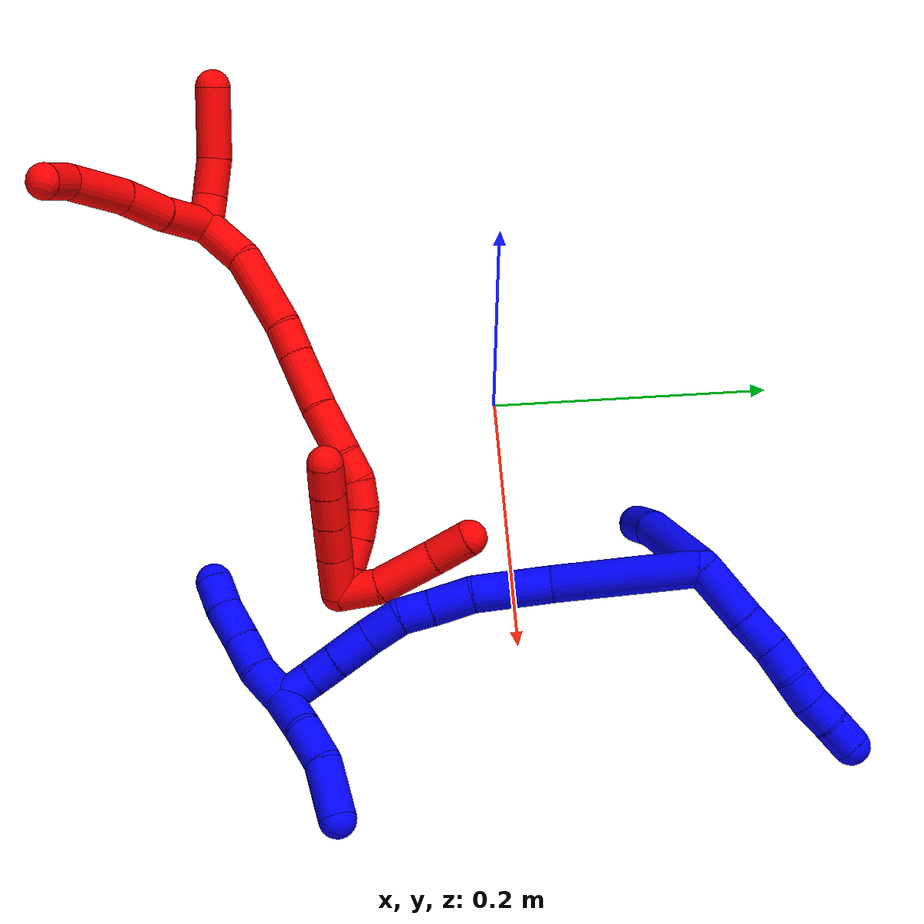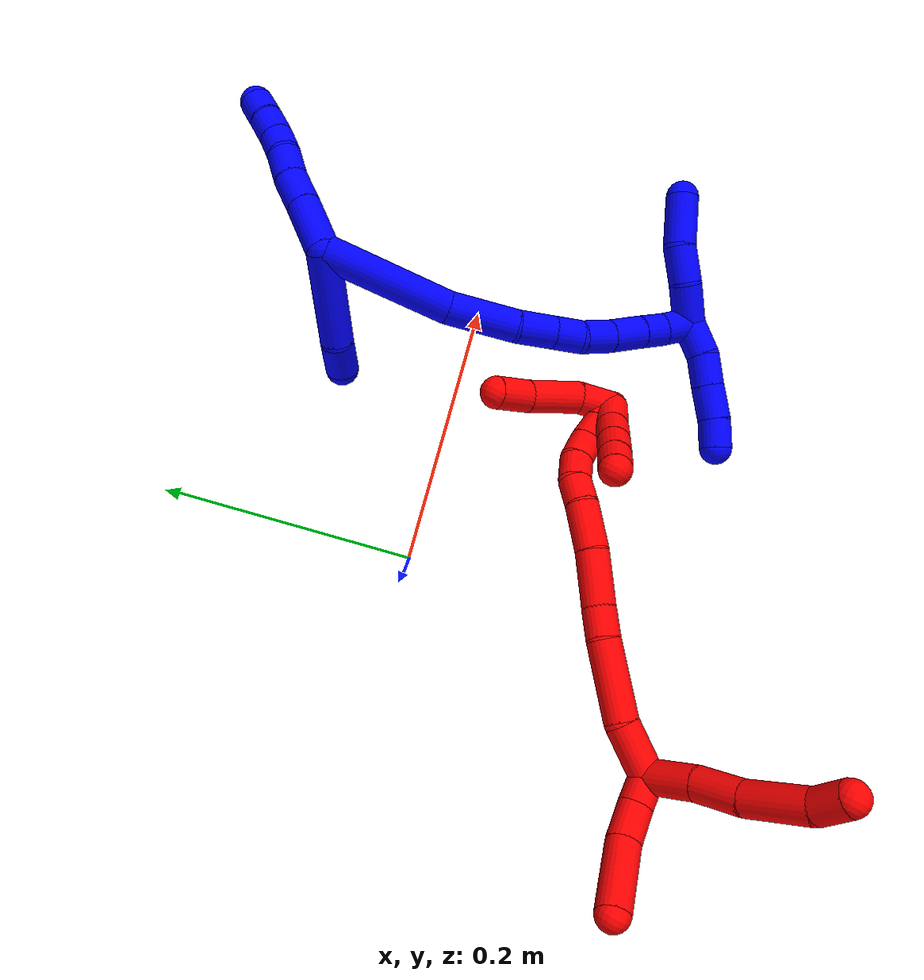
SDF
<sdf version="1.7">
 <world name="default">
  <plugin name="TubeGeneratorPlugin" filename="libtube_generator_plugin.so"/>
  <model name="photoneo_s_sensor">
   <static>1</static>
   <pose>0 0 2 1.57079 1.57079 3.14159</pose>
   <link name="link">
    <inertial><mass>0.1</mass></inertial>
    <sensor name="sensor" type="depth">
     <update_rate>30</update_rate>
     <camera>
      <horizontal_fov>1.22</horizontal_fov>
      <image><width>1920</width><height>1200</height><format>B8G8R8</format></image>
      <clip><near>0.1</near><far>4</far></clip>
      <depth_camera><output>points</output></depth_camera>
     </camera>
     <plugin name="camera_plugin" filename="libgazebo_ros_depth_camera.so">
      <baseline>0.2</baseline>
      <alwaysOn>1</alwaysOn>
      <updateRate>0.0</updateRate>
      <cameraName>camera_ir</cameraName>
      <imageTopicName>/camera/color/image_raw</imageTopicName>
      <cameraInfoTopicName>/camera/color/camera_info</cameraInfoTopicName>
      <depthImageTopicName>/camera/depth/image_raw</depthImageTopicName>
      <depthImageCameraInfoTopicName>/camera/depth/camera_info</depthImageCameraInfoTopicName>
      <pointCloudTopicName>/camera/depth/points</pointCloudTopicName>
      <frameName>fr_optical</frameName>
      <pointCloudCutoff>0.1</pointCloudCutoff>
      <pointCloudCutoffMax>2.0</pointCloudCutoffMax>
      <distortionK1>0</distortionK1>
      <distortionK2>0</distortionK2>
      <distortionK3>0</distortionK3>
      <distortionT1>0</distortionT1>
      <distortionT2>0</distortionT2>
      <CxPrime>0</CxPrime>
      <Cx>0</Cx>
      <Cy>0</Cy>
      <focalLength>0</focalLength>
      <hackBaseline>0</hackBaseline>
     </plugin>
    </sensor>
   </link>
  </model>
  <gravity>0 0 -9.8</gravity>
  <magnetic_field>6e-06 2.3e-05 -4.2e-05</magnetic_field>
  <atmosphere type="adiabatic"/>
  <physics name="default_physics" default="0" type="ode">
   <max_step_size>0.003</max_step_size>
   <real_time_factor>1</real_time_factor>
   <real_time_update_rate>1000</real_time_update_rate>
   <max_contacts>10000</max_contacts>
   <ode>
    <solver>
     <type>quick</type>
     <iters>100</iters>
     <sor>1.3</sor>
     <use_dynamic_moi_rescaling>0</use_dynamic_moi_rescaling>
    </solver>
    <constraints>
     <contact_max_correcting_vel>0</contact_max_correcting_vel>
     <contact_surface_layer>0.001</contact_surface_layer>
     <cfm>0</cfm>
     <erp>0.2</erp>
    </constraints>
   </ode>
  </physics>
  <scene><ambient>0.4 0.4 0.4 1</ambient><background>0.7 0.7 0.7 1</background><shadows>0</shadows></scene>
  <audio><device>default</device></audio>
  <spherical_coordinates>
   <surface_model>EARTH_WGS84</surface_model>
   <latitude_deg>0</latitude_deg>
   <longitude_deg>0</longitude_deg>
   <elevation>0</elevation>
   <heading_deg>0</heading_deg>
  </spherical_coordinates>
  <model name="bin">
   <static>1</static>
   <link name="bottom">
    <collision name="collision-bottom">
     <pose>0 0 -0.01 0 -0 0</pose>
     <geometry><box><size>0.8 0.6 0.02</size></box></geometry>
     <surface>
      <friction><ode><mu>100</mu><mu2>100</mu2></ode></friction>
      <contact><collide_bitmask>65535</collide_bitmask></contact>
     </surface>
    </collision>
   </link>
   <link name="west_wall">
    <collision name="collision-west_wall">
     <pose>-0.41 0 0.1 0 -0 0</pose>
     <geometry><box><size>0.02 0.6 0.2</size></box></geometry>
     <surface>
      <friction><ode><mu>100</mu><mu2>100</mu2></ode></friction>
      <contact><collide_bitmask>65535</collide_bitmask></contact>
     </surface>
    </collision>
   </link>
   <link name="east_wall">
    <collision name="collision-east_wall">
     <pose>0.41 0 0.1 0 -0 0</pose>
     <geometry><box><size>0.02 0.6 0.2</size></box></geometry>
     <surface>
      <friction><ode><mu>100</mu><mu2>100</mu2></ode></friction>
      <contact><collide_bitmask>65535</collide_bitmask></contact>
     </surface>
    </collision>
   </link>
   <link name="south_wall">
    <collision name="collision-south_wall">
     <pose>0 -0.31 0.1 0 -0 0</pose>
     <geometry><box><size>0.8 0.02 0.2</size></box></geometry>
     <surface>
      <friction><ode><mu>100</mu><mu2>100</mu2></ode></friction>
      <contact><collide_bitmask>65535</collide_bitmask></contact>
     </surface>
    </collision>
   </link>
   <link name="north_wall">
    <collision name="collision-north_wall">
     <pose>0 0.31 0.1 0 -0 0</pose>
     <geometry><box><size>0.8 0.02 0.2</size></box></geometry>
     <surface>
      <friction><ode><mu>100</mu><mu2>100</mu2></ode></friction>
      <contact><collide_bitmask>65535</collide_bitmask></contact>
     </surface>
    </collision>
   </link>
  </model>
  <model name="1">
   <static>0</static>
   <link name="1">
    <collision name="collision-cylinder-e_1_2_8">
     <pose>0.013728 0.008758 0.012895 -0.596623 0.722049 -0.231163</pose>
     <geometry><cylinder><radius>0.0125</radius><length>0.041543</length></cylinder></geometry>
     <surface>
      <friction><ode><mu>1.16</mu><mu2>1.16</mu2><slip1>0</slip1><slip2>0</slip2></ode></friction>
      <contact><ode><kp>1e+06</kp><kd>1</kd><max_vel>0</max_vel><min_depth>0.001</min_depth></ode></contact>
     </surface>
    </collision>
    <visual name="visual-cylinder-e_1_2_8">
     <pose>0.013728 0.008758 0.012895 -0.596623 0.722049 -0.231163</pose>
     <geometry><cylinder><radius>0.0125</radius><length>0.041543</length></cylinder></geometry>
     <material><ambient>0 0 1 1</ambient></material>
    </visual>
    <collision name="collision-cylinder-e_2_8_9">
     <pose>0.035744 0.023323 0.033961 -0.617864 0.690821 -0.228682</pose>
     <geometry><cylinder><radius>0.0125</radius><length>0.026012</length></cylinder></geometry>
     <surface>
      <friction><ode><mu>1.16</mu><mu2>1.16</mu2><slip1>0</slip1><slip2>0</slip2></ode></friction>
      <contact><ode><kp>1e+06</kp><kd>1</kd><max_vel>0</max_vel><min_depth>0.001</min_depth></ode></contact>
     </surface>
    </collision>
    <visual name="visual-cylinder-e_2_8_9">
     <pose>0.035744 0.023323 0.033961 -0.617864 0.690821 -0.228682</pose>
     <geometry><cylinder><radius>0.0125</radius><length>0.026012</length></cylinder></geometry>
     <material><ambient>0 0 1 1</ambient></material>
    </visual>
    <collision name="collision-cylinder-e_3_9_10">
     <pose>0.051557 0.03265 0.049611 -0.439895 0.738585 -0.172631</pose>
     <geometry><cylinder><radius>0.0125</radius><length>0.022359</length></cylinder></geometry>
     <surface>
      <friction><ode><mu>1.16</mu><mu2>1.16</mu2><slip1>0</slip1><slip2>0</slip2></ode></friction>
      <contact><ode><kp>1e+06</kp><kd>1</kd><max_vel>0</max_vel><min_depth>0.001</min_depth></ode></contact>
     </surface>
    </collision>
    <visual name="visual-cylinder-e_3_9_10">
     <pose>0.051557 0.03265 0.049611 -0.439895 0.738585 -0.172631</pose>
     <geometry><cylinder><radius>0.0125</radius><length>0.022359</length></cylinder></geometry>
     <material><ambient>0 0 1 1</ambient></material>
    </visual>
    <collision name="collision-cylinder-e_4_10_11">
     <pose>0.066774 0.040418 0.061917 -0.721678 0.874472 -0.349172</pose>
     <geometry><cylinder><radius>0.0125</radius><length>0.020046</length></cylinder></geometry>
     <surface>
      <friction><ode><mu>1.16</mu><mu2>1.16</mu2><slip1>0</slip1><slip2>0</slip2></ode></friction>
      <contact><ode><kp>1e+06</kp><kd>1</kd><max_vel>0</max_vel><min_depth>0.001</min_depth></ode></contact>
     </surface>
    </collision>
    <visual name="visual-cylinder-e_4_10_11">
     <pose>0.066774 0.040418 0.061917 -0.721678 0.874472 -0.349172</pose>
     <geometry><cylinder><radius>0.0125</radius><length>0.020046</length></cylinder></geometry>
     <material><ambient>0 0 1 1</ambient></material>
    </visual>
    <collision name="collision-cylinder-e_5_11_12">
     <pose>0.080775 0.049559 0.072764 -0.682514 0.682811 -0.251057</pose>
     <geometry><cylinder><radius>0.0125</radius><length>0.020005</length></cylinder></geometry>
     <surface>
      <friction><ode><mu>1.16</mu><mu2>1.16</mu2><slip1>0</slip1><slip2>0</slip2></ode></friction>
      <contact><ode><kp>1e+06</kp><kd>1</kd><max_vel>0</max_vel><min_depth>0.001</min_depth></ode></contact>
     </surface>
    </collision>
    <visual name="visual-cylinder-e_5_11_12">
     <pose>0.080775 0.049559 0.072764 -0.682514 0.682811 -0.251057</pose>
     <geometry><cylinder><radius>0.0125</radius><length>0.020005</length></cylinder></geometry>
     <material><ambient>0 0 1 1</ambient></material>
    </visual>
    <collision name="collision-cylinder-e_6_12_6">
     <pose>0.094128 0.059588 0.083726 -0.804596 0.779516 -0.346075</pose>
     <geometry><cylinder><radius>0.0125</radius><length>0.020035</length></cylinder></geometry>
     <surface>
      <friction><ode><mu>1.16</mu><mu2>1.16</mu2><slip1>0</slip1><slip2>0</slip2></ode></friction>
      <contact><ode><kp>1e+06</kp><kd>1</kd><max_vel>0</max_vel><min_depth>0.001</min_depth></ode></contact>
     </surface>
    </collision>
    <visual name="visual-cylinder-e_6_12_6">
     <pose>0.094128 0.059588 0.083726 -0.804596 0.779516 -0.346075</pose>
     <geometry><cylinder><radius>0.0125</radius><length>0.020035</length></cylinder></geometry>
     <material><ambient>0 0 1 1</ambient></material>
    </visual>
    <collision name="collision-cylinder-e_1_2_13">
     <pose>0.003373 0.002211 -0.036047 -3.08033 0.093113 -1.97802</pose>
     <geometry><cylinder><radius>0.0125</radius><length>0.072544</length></cylinder></geometry>
     <surface>
      <friction><ode><mu>1.16</mu><mu2>1.16</mu2><slip1>0</slip1><slip2>0</slip2></ode></friction>
      <contact><ode><kp>1e+06</kp><kd>1</kd><max_vel>0</max_vel><min_depth>0.001</min_depth></ode></contact>
     </surface>
    </collision>
    <visual name="visual-cylinder-e_1_2_13">
     <pose>0.003373 0.002211 -0.036047 -3.08033 0.093113 -1.97802</pose>
     <geometry><cylinder><radius>0.0125</radius><length>0.072544</length></cylinder></geometry>
     <material><ambient>0 0 1 1</ambient></material>
    </visual>
    <collision name="collision-cylinder-e_2_13_5">
     <pose>0.01133 0.005926 -0.084946 -3.02513 0.340565 -2.48782</pose>
     <geometry><cylinder><radius>0.0125</radius><length>0.027456</length></cylinder></geometry>
     <surface>
      <friction><ode><mu>1.16</mu><mu2>1.16</mu2><slip1>0</slip1><slip2>0</slip2></ode></friction>
      <contact><ode><kp>1e+06</kp><kd>1</kd><max_vel>0</max_vel><min_depth>0.001</min_depth></ode></contact>
     </surface>
    </collision>
    <visual name="visual-cylinder-e_2_13_5">
     <pose>0.01133 0.005926 -0.084946 -3.02513 0.340565 -2.48782</pose>
     <geometry><cylinder><radius>0.0125</radius><length>0.027456</length></cylinder></geometry>
     <material><ambient>0 0 1 1</ambient></material>
    </visual>
    <collision name="collision-cylinder-e_1_2_14">
     <pose>0.011297 -0.039592 -0.028262 2.19075 0.228188 0.438043</pose>
     <geometry><cylinder><radius>0.0125</radius><length>0.099877</length></cylinder></geometry>
     <surface>
      <friction><ode><mu>1.16</mu><mu2>1.16</mu2><slip1>0</slip1><slip2>0</slip2></ode></friction>
      <contact><ode><kp>1e+06</kp><kd>1</kd><max_vel>0</max_vel><min_depth>0.001</min_depth></ode></contact>
     </surface>
    </collision>
    <visual name="visual-cylinder-e_1_2_14">
     <pose>0.011297 -0.039592 -0.028262 2.19075 0.228188 0.438043</pose>
     <geometry><cylinder><radius>0.0125</radius><length>0.099877</length></cylinder></geometry>
     <material><ambient>0 0 1 1</ambient></material>
    </visual>
    <collision name="collision-cylinder-e_2_14_15">
     <pose>0.026235 -0.103539 -0.06694 1.97492 0.136614 0.206592</pose>
     <geometry><cylinder><radius>0.0125</radius><length>0.053476</length></cylinder></geometry>
     <surface>
      <friction><ode><mu>1.16</mu><mu2>1.16</mu2><slip1>0</slip1><slip2>0</slip2></ode></friction>
      <contact><ode><kp>1e+06</kp><kd>1</kd><max_vel>0</max_vel><min_depth>0.001</min_depth></ode></contact>
     </surface>
    </collision>
    <visual name="visual-cylinder-e_2_14_15">
     <pose>0.026235 -0.103539 -0.06694 1.97492 0.136614 0.206592</pose>
     <geometry><cylinder><radius>0.0125</radius><length>0.053476</length></cylinder></geometry>
     <material><ambient>0 0 1 1</ambient></material>
    </visual>
    <collision name="collision-cylinder-e_3_15_16">
     <pose>0.034658 -0.140536 -0.082424 1.9521 0.337605 0.493603</pose>
     <geometry><cylinder><radius>0.0125</radius><length>0.028871</length></cylinder></geometry>
     <surface>
      <friction><ode><mu>1.16</mu><mu2>1.16</mu2><slip1>0</slip1><slip2>0</slip2></ode></friction>
      <contact><ode><kp>1e+06</kp><kd>1</kd><max_vel>0</max_vel><min_depth>0.001</min_depth></ode></contact>
     </surface>
    </collision>
    <visual name="visual-cylinder-e_3_15_16">
     <pose>0.034658 -0.140536 -0.082424 1.9521 0.337605 0.493603</pose>
     <geometry><cylinder><radius>0.0125</radius><length>0.028871</length></cylinder></geometry>
     <material><ambient>0 0 1 1</ambient></material>
    </visual>
    <collision name="collision-cylinder-e_4_16_17">
     <pose>0.042314 -0.162908 -0.091111 1.92685 0.270188 0.38626</pose>
     <geometry><cylinder><radius>0.0125</radius><length>0.021541</length></cylinder></geometry>
     <surface>
      <friction><ode><mu>1.16</mu><mu2>1.16</mu2><slip1>0</slip1><slip2>0</slip2></ode></friction>
      <contact><ode><kp>1e+06</kp><kd>1</kd><max_vel>0</max_vel><min_depth>0.001</min_depth></ode></contact>
     </surface>
    </collision>
    <visual name="visual-cylinder-e_4_16_17">
     <pose>0.042314 -0.162908 -0.091111 1.92685 0.270188 0.38626</pose>
     <geometry><cylinder><radius>0.0125</radius><length>0.021541</length></cylinder></geometry>
     <material><ambient>0 0 1 1</ambient></material>
    </visual>
    <collision name="collision-cylinder-e_5_17_18">
     <pose>0.05213 -0.182556 -0.097745 1.86595 0.589925 0.778076</pose>
     <geometry><cylinder><radius>0.0125</radius><length>0.024954</length></cylinder></geometry>
     <surface>
      <friction><ode><mu>1.16</mu><mu2>1.16</mu2><slip1>0</slip1><slip2>0</slip2></ode></friction>
      <contact><ode><kp>1e+06</kp><kd>1</kd><max_vel>0</max_vel><min_depth>0.001</min_depth></ode></contact>
     </surface>
    </collision>
    <visual name="visual-cylinder-e_5_17_18">
     <pose>0.05213 -0.182556 -0.097745 1.86595 0.589925 0.778076</pose>
     <geometry><cylinder><radius>0.0125</radius><length>0.024954</length></cylinder></geometry>
     <material><ambient>0 0 1 1</ambient></material>
    </visual>
    <collision name="collision-cylinder-e_6_18_19">
     <pose>0.066859 -0.203681 -0.102839 1.75418 0.599526 0.711699</pose>
     <geometry><cylinder><radius>0.0125</radius><length>0.027607</length></cylinder></geometry>
     <surface>
      <friction><ode><mu>1.16</mu><mu2>1.16</mu2><slip1>0</slip1><slip2>0</slip2></ode></friction>
      <contact><ode><kp>1e+06</kp><kd>1</kd><max_vel>0</max_vel><min_depth>0.001</min_depth></ode></contact>
     </surface>
    </collision>
    <visual name="visual-cylinder-e_6_18_19">
     <pose>0.066859 -0.203681 -0.102839 1.75418 0.599526 0.711699</pose>
     <geometry><cylinder><radius>0.0125</radius><length>0.027607</length></cylinder></geometry>
     <material><ambient>0 0 1 1</ambient></material>
    </visual>
    <collision name="collision-cylinder-e_7_19_20">
     <pose>0.080375 -0.222984 -0.10665 1.78162 0.605057 0.736706</pose>
     <geometry><cylinder><radius>0.0125</radius><length>0.020136</length></cylinder></geometry>
     <surface>
      <friction><ode><mu>1.16</mu><mu2>1.16</mu2><slip1>0</slip1><slip2>0</slip2></ode></friction>
      <contact><ode><kp>1e+06</kp><kd>1</kd><max_vel>0</max_vel><min_depth>0.001</min_depth></ode></contact>
     </surface>
    </collision>
    <visual name="visual-cylinder-e_7_19_20">
     <pose>0.080375 -0.222984 -0.10665 1.78162 0.605057 0.736706</pose>
     <geometry><cylinder><radius>0.0125</radius><length>0.020136</length></cylinder></geometry>
     <material><ambient>0 0 1 1</ambient></material>
    </visual>
    <collision name="collision-cylinder-e_8_20_1">
     <pose>0.091926 -0.241286 -0.109046 1.63562 0.517683 0.550703</pose>
     <geometry><cylinder><radius>0.0125</radius><length>0.023537</length></cylinder></geometry>
     <surface>
      <friction><ode><mu>1.16</mu><mu2>1.16</mu2><slip1>0</slip1><slip2>0</slip2></ode></friction>
      <contact><ode><kp>1e+06</kp><kd>1</kd><max_vel>0</max_vel><min_depth>0.001</min_depth></ode></contact>
     </surface>
    </collision>
    <visual name="visual-cylinder-e_8_20_1">
     <pose>0.091926 -0.241286 -0.109046 1.63562 0.517683 0.550703</pose>
     <geometry><cylinder><radius>0.0125</radius><length>0.023537</length></cylinder></geometry>
     <material><ambient>0 0 1 1</ambient></material>
    </visual>
    <collision name="collision-cylinder-e_1_1_21">
     <pose>0.091453 -0.256403 -0.120633 2.71902 -0.483973 -1.71075</pose>
     <geometry><cylinder><radius>0.0125</radius><length>0.027065</length></cylinder></geometry>
     <surface>
      <friction><ode><mu>1.16</mu><mu2>1.16</mu2><slip1>0</slip1><slip2>0</slip2></ode></friction>
      <contact><ode><kp>1e+06</kp><kd>1</kd><max_vel>0</max_vel><min_depth>0.001</min_depth></ode></contact>
     </surface>
    </collision>
    <visual name="visual-cylinder-e_1_1_21">
     <pose>0.091453 -0.256403 -0.120633 2.71902 -0.483973 -1.71075</pose>
     <geometry><cylinder><radius>0.0125</radius><length>0.027065</length></cylinder></geometry>
     <material><ambient>0 0 1 1</ambient></material>
    </visual>
    <collision name="collision-cylinder-e_2_21_22">
     <pose>0.078914 -0.262734 -0.14201 3.00671 -0.534367 -2.65774</pose>
     <geometry><cylinder><radius>0.0125</radius><length>0.024514</length></cylinder></geometry>
     <surface>
      <friction><ode><mu>1.16</mu><mu2>1.16</mu2><slip1>0</slip1><slip2>0</slip2></ode></friction>
      <contact><ode><kp>1e+06</kp><kd>1</kd><max_vel>0</max_vel><min_depth>0.001</min_depth></ode></contact>
     </surface>
    </collision>
    <visual name="visual-cylinder-e_2_21_22">
     <pose>0.078914 -0.262734 -0.14201 3.00671 -0.534367 -2.65774</pose>
     <geometry><cylinder><radius>0.0125</radius><length>0.024514</length></cylinder></geometry>
     <material><ambient>0 0 1 1</ambient></material>
    </visual>
    <collision name="collision-cylinder-e_3_22_23">
     <pose>0.065945 -0.266202 -0.16356 2.95902 -0.537534 -2.49986</pose>
     <geometry><cylinder><radius>0.0125</radius><length>0.026275</length></cylinder></geometry>
     <surface>
      <friction><ode><mu>1.16</mu><mu2>1.16</mu2><slip1>0</slip1><slip2>0</slip2></ode></friction>
      <contact><ode><kp>1e+06</kp><kd>1</kd><max_vel>0</max_vel><min_depth>0.001</min_depth></ode></contact>
     </surface>
    </collision>
    <visual name="visual-cylinder-e_3_22_23">
     <pose>0.065945 -0.266202 -0.16356 2.95902 -0.537534 -2.49986</pose>
     <geometry><cylinder><radius>0.0125</radius><length>0.026275</length></cylinder></geometry>
     <material><ambient>0 0 1 1</ambient></material>
    </visual>
    <collision name="collision-cylinder-e_4_23_4">
     <pose>0.053225 -0.268399 -0.183967 3.12567 -0.57191 -3.08744</pose>
     <geometry><cylinder><radius>0.0125</radius><length>0.022146</length></cylinder></geometry>
     <surface>
      <friction><ode><mu>1.16</mu><mu2>1.16</mu2><slip1>0</slip1><slip2>0</slip2></ode></friction>
      <contact><ode><kp>1e+06</kp><kd>1</kd><max_vel>0</max_vel><min_depth>0.001</min_depth></ode></contact>
     </surface>
    </collision>
    <visual name="visual-cylinder-e_4_23_4">
     <pose>0.053225 -0.268399 -0.183967 3.12567 -0.57191 -3.08744</pose>
     <geometry><cylinder><radius>0.0125</radius><length>0.022146</length></cylinder></geometry>
     <material><ambient>0 0 1 1</ambient></material>
    </visual>
    <collision name="collision-cylinder-e_1_1_24">
     <pose>0.100212 -0.250635 -0.094115 -0.054848 0.156387 -0.004299</pose>
     <geometry><cylinder><radius>0.0125</radius><length>0.03162</length></cylinder></geometry>
     <surface>
      <friction><ode><mu>1.16</mu><mu2>1.16</mu2><slip1>0</slip1><slip2>0</slip2></ode></friction>
      <contact><ode><kp>1e+06</kp><kd>1</kd><max_vel>0</max_vel><min_depth>0.001</min_depth></ode></contact>
     </surface>
    </collision>
    <visual name="visual-cylinder-e_1_1_24">
     <pose>0.100212 -0.250635 -0.094115 -0.054848 0.156387 -0.004299</pose>
     <geometry><cylinder><radius>0.0125</radius><length>0.03162</length></cylinder></geometry>
     <material><ambient>0 0 1 1</ambient></material>
    </visual>
    <collision name="collision-cylinder-e_2_24_25">
     <pose>0.108447 -0.248068 -0.065423 -0.129921 0.412006 -0.027186</pose>
     <geometry><cylinder><radius>0.0125</radius><length>0.028831</length></cylinder></geometry>
     <surface>
      <friction><ode><mu>1.16</mu><mu2>1.16</mu2><slip1>0</slip1><slip2>0</slip2></ode></friction>
      <contact><ode><kp>1e+06</kp><kd>1</kd><max_vel>0</max_vel><min_depth>0.001</min_depth></ode></contact>
     </surface>
    </collision>
    <visual name="visual-cylinder-e_2_24_25">
     <pose>0.108447 -0.248068 -0.065423 -0.129921 0.412006 -0.027186</pose>
     <geometry><cylinder><radius>0.0125</radius><length>0.028831</length></cylinder></geometry>
     <material><ambient>0 0 1 1</ambient></material>
    </visual>
    <collision name="collision-cylinder-e_3_25_3">
     <pose>0.125781 -0.247923 -0.03636 0.097821 0.624482 0.031599</pose>
     <geometry><cylinder><radius>0.0125</radius><length>0.039549</length></cylinder></geometry>
     <surface>
      <friction><ode><mu>1.16</mu><mu2>1.16</mu2><slip1>0</slip1><slip2>0</slip2></ode></friction>
      <contact><ode><kp>1e+06</kp><kd>1</kd><max_vel>0</max_vel><min_depth>0.001</min_depth></ode></contact>
     </surface>
    </collision>
    <visual name="visual-cylinder-e_3_25_3">
     <pose>0.125781 -0.247923 -0.03636 0.097821 0.624482 0.031599</pose>
     <geometry><cylinder><radius>0.0125</radius><length>0.039549</length></cylinder></geometry>
     <material><ambient>0 0 1 1</ambient></material>
    </visual>
    <collision name="collision-sphere-3">
     <pose>0.137343 -0.24949 -0.020394 0 -0 0</pose>
     <geometry><sphere><radius>0.0125</radius></sphere></geometry>
     <surface>
      <friction><ode><mu>1.16</mu><mu2>1.16</mu2><slip1>0</slip1><slip2>0</slip2></ode></friction>
      <contact><ode><kp>1e+06</kp><kd>1</kd><max_vel>0</max_vel><min_depth>0.001</min_depth></ode></contact>
     </surface>
    </collision>
    <visual name="visual-sphere-3">
     <pose>0.137343 -0.24949 -0.020394 0 -0 0</pose>
     <geometry><sphere><radius>0.0125</radius></sphere></geometry>
     <material><ambient>0 0 1 1</ambient></material>
    </visual>
    <collision name="collision-sphere-25">
     <pose>0.11422 -0.246356 -0.052325 0 -0 0</pose>
     <geometry><sphere><radius>0.0125</radius></sphere></geometry>
     <surface>
      <friction><ode><mu>1.16</mu><mu2>1.16</mu2><slip1>0</slip1><slip2>0</slip2></ode></friction>
      <contact><ode><kp>1e+06</kp><kd>1</kd><max_vel>0</max_vel><min_depth>0.001</min_depth></ode></contact>
     </surface>
    </collision>
    <visual name="visual-sphere-25">
     <pose>0.11422 -0.246356 -0.052325 0 -0 0</pose>
     <geometry><sphere><radius>0.0125</radius></sphere></geometry>
     <material><ambient>0 0 1 1</ambient></material>
    </visual>
    <collision name="collision-sphere-24">
     <pose>0.102674 -0.249779 -0.078521 0 -0 0</pose>
     <geometry><sphere><radius>0.0125</radius></sphere></geometry>
     <surface>
      <friction><ode><mu>1.16</mu><mu2>1.16</mu2><slip1>0</slip1><slip2>0</slip2></ode></friction>
      <contact><ode><kp>1e+06</kp><kd>1</kd><max_vel>0</max_vel><min_depth>0.001</min_depth></ode></contact>
     </surface>
    </collision>
    <visual name="visual-sphere-24">
     <pose>0.102674 -0.249779 -0.078521 0 -0 0</pose>
     <geometry><sphere><radius>0.0125</radius></sphere></geometry>
     <material><ambient>0 0 1 1</ambient></material>
    </visual>
    <collision name="collision-sphere-4">
     <pose>0.047232 -0.268547 -0.193277 0 -0 0</pose>
     <geometry><sphere><radius>0.0125</radius></sphere></geometry>
     <surface>
      <friction><ode><mu>1.16</mu><mu2>1.16</mu2><slip1>0</slip1><slip2>0</slip2></ode></friction>
      <contact><ode><kp>1e+06</kp><kd>1</kd><max_vel>0</max_vel><min_depth>0.001</min_depth></ode></contact>
     </surface>
    </collision>
    <visual name="visual-sphere-4">
     <pose>0.047232 -0.268547 -0.193277 0 -0 0</pose>
     <geometry><sphere><radius>0.0125</radius></sphere></geometry>
     <material><ambient>0 0 1 1</ambient></material>
    </visual>
    <collision name="collision-sphere-23">
     <pose>0.059218 -0.26825 -0.174657 0 -0 0</pose>
     <geometry><sphere><radius>0.0125</radius></sphere></geometry>
     <surface>
      <friction><ode><mu>1.16</mu><mu2>1.16</mu2><slip1>0</slip1><slip2>0</slip2></ode></friction>
      <contact><ode><kp>1e+06</kp><kd>1</kd><max_vel>0</max_vel><min_depth>0.001</min_depth></ode></contact>
     </surface>
    </collision>
    <visual name="visual-sphere-23">
     <pose>0.059218 -0.26825 -0.174657 0 -0 0</pose>
     <geometry><sphere><radius>0.0125</radius></sphere></geometry>
     <material><ambient>0 0 1 1</ambient></material>
    </visual>
    <collision name="collision-sphere-22">
     <pose>0.072671 -0.264153 -0.152462 0 -0 0</pose>
     <geometry><sphere><radius>0.0125</radius></sphere></geometry>
     <surface>
      <friction><ode><mu>1.16</mu><mu2>1.16</mu2><slip1>0</slip1><slip2>0</slip2></ode></friction>
      <contact><ode><kp>1e+06</kp><kd>1</kd><max_vel>0</max_vel><min_depth>0.001</min_depth></ode></contact>
     </surface>
    </collision>
    <visual name="visual-sphere-22">
     <pose>0.072671 -0.264153 -0.152462 0 -0 0</pose>
     <geometry><sphere><radius>0.0125</radius></sphere></geometry>
     <material><ambient>0 0 1 1</ambient></material>
    </visual>
    <collision name="collision-sphere-21">
     <pose>0.085156 -0.261316 -0.131558 0 -0 0</pose>
     <geometry><sphere><radius>0.0125</radius></sphere></geometry>
     <surface>
      <friction><ode><mu>1.16</mu><mu2>1.16</mu2><slip1>0</slip1><slip2>0</slip2></ode></friction>
      <contact><ode><kp>1e+06</kp><kd>1</kd><max_vel>0</max_vel><min_depth>0.001</min_depth></ode></contact>
     </surface>
    </collision>
    <visual name="visual-sphere-21">
     <pose>0.085156 -0.261316 -0.131558 0 -0 0</pose>
     <geometry><sphere><radius>0.0125</radius></sphere></geometry>
     <material><ambient>0 0 1 1</ambient></material>
    </visual>
    <collision name="collision-sphere-1">
     <pose>0.09775 -0.251491 -0.109708 0 -0 0</pose>
     <geometry><sphere><radius>0.0125</radius></sphere></geometry>
     <surface>
      <friction><ode><mu>1.16</mu><mu2>1.16</mu2><slip1>0</slip1><slip2>0</slip2></ode></friction>
      <contact><ode><kp>1e+06</kp><kd>1</kd><max_vel>0</max_vel><min_depth>0.001</min_depth></ode></contact>
     </surface>
    </collision>
    <visual name="visual-sphere-1">
     <pose>0.09775 -0.251491 -0.109708 0 -0 0</pose>
     <geometry><sphere><radius>0.0125</radius></sphere></geometry>
     <material><ambient>0 0 1 1</ambient></material>
    </visual>
    <collision name="collision-sphere-12">
     <pose>0.087086 0.054454 0.078786 0 -0 0</pose>
     <geometry><sphere><radius>0.0125</radius></sphere></geometry>
     <surface>
      <friction><ode><mu>1.16</mu><mu2>1.16</mu2><slip1>0</slip1><slip2>0</slip2></ode></friction>
      <contact><ode><kp>1e+06</kp><kd>1</kd><max_vel>0</max_vel><min_depth>0.001</min_depth></ode></contact>
     </surface>
    </collision>
    <visual name="visual-sphere-12">
     <pose>0.087086 0.054454 0.078786 0 -0 0</pose>
     <geometry><sphere><radius>0.0125</radius></sphere></geometry>
     <material><ambient>0 0 1 1</ambient></material>
    </visual>
    <collision name="collision-sphere-11">
     <pose>0.074463 0.044665 0.066743 0 -0 0</pose>
     <geometry><sphere><radius>0.0125</radius></sphere></geometry>
     <surface>
      <friction><ode><mu>1.16</mu><mu2>1.16</mu2><slip1>0</slip1><slip2>0</slip2></ode></friction>
      <contact><ode><kp>1e+06</kp><kd>1</kd><max_vel>0</max_vel><min_depth>0.001</min_depth></ode></contact>
     </surface>
    </collision>
    <visual name="visual-sphere-11">
     <pose>0.074463 0.044665 0.066743 0 -0 0</pose>
     <geometry><sphere><radius>0.0125</radius></sphere></geometry>
     <material><ambient>0 0 1 1</ambient></material>
    </visual>
    <collision name="collision-sphere-10">
     <pose>0.059084 0.036171 0.057091 0 -0 0</pose>
     <geometry><sphere><radius>0.0125</radius></sphere></geometry>
     <surface>
      <friction><ode><mu>1.16</mu><mu2>1.16</mu2><slip1>0</slip1><slip2>0</slip2></ode></friction>
      <contact><ode><kp>1e+06</kp><kd>1</kd><max_vel>0</max_vel><min_depth>0.001</min_depth></ode></contact>
     </surface>
    </collision>
    <visual name="visual-sphere-10">
     <pose>0.059084 0.036171 0.057091 0 -0 0</pose>
     <geometry><sphere><radius>0.0125</radius></sphere></geometry>
     <material><ambient>0 0 1 1</ambient></material>
    </visual>
    <collision name="collision-sphere-9">
     <pose>0.044031 0.02913 0.042132 0 -0 0</pose>
     <geometry><sphere><radius>0.0125</radius></sphere></geometry>
     <surface>
      <friction><ode><mu>1.16</mu><mu2>1.16</mu2><slip1>0</slip1><slip2>0</slip2></ode></friction>
      <contact><ode><kp>1e+06</kp><kd>1</kd><max_vel>0</max_vel><min_depth>0.001</min_depth></ode></contact>
     </surface>
    </collision>
    <visual name="visual-sphere-9">
     <pose>0.044031 0.02913 0.042132 0 -0 0</pose>
     <geometry><sphere><radius>0.0125</radius></sphere></geometry>
     <material><ambient>0 0 1 1</ambient></material>
    </visual>
    <collision name="collision-sphere-2">
     <geometry><sphere><radius>0.0125</radius></sphere></geometry>
     <surface>
      <friction><ode><mu>1.16</mu><mu2>1.16</mu2><slip1>0</slip1><slip2>0</slip2></ode></friction>
      <contact><ode><kp>1e+06</kp><kd>1</kd><max_vel>0</max_vel><min_depth>0.001</min_depth></ode></contact>
     </surface>
    </collision>
    <visual name="visual-sphere-2">
     <geometry><sphere><radius>0.0125</radius></sphere></geometry>
     <material><ambient>0 0 1 1</ambient></material>
    </visual>
    <collision name="collision-sphere-19">
     <pose>0.074648 -0.214886 -0.104918 0 -0 0</pose>
     <geometry><sphere><radius>0.0125</radius></sphere></geometry>
     <surface>
      <friction><ode><mu>1.16</mu><mu2>1.16</mu2><slip1>0</slip1><slip2>0</slip2></ode></friction>
      <contact><ode><kp>1e+06</kp><kd>1</kd><max_vel>0</max_vel><min_depth>0.001</min_depth></ode></contact>
     </surface>
    </collision>
    <visual name="visual-sphere-19">
     <pose>0.074648 -0.214886 -0.104918 0 -0 0</pose>
     <geometry><sphere><radius>0.0125</radius></sphere></geometry>
     <material><ambient>0 0 1 1</ambient></material>
    </visual>
    <collision name="collision-sphere-8">
     <pose>0.027457 0.017516 0.02579 0 -0 0</pose>
     <geometry><sphere><radius>0.0125</radius></sphere></geometry>
     <surface>
      <friction><ode><mu>1.16</mu><mu2>1.16</mu2><slip1>0</slip1><slip2>0</slip2></ode></friction>
      <contact><ode><kp>1e+06</kp><kd>1</kd><max_vel>0</max_vel><min_depth>0.001</min_depth></ode></contact>
     </surface>
    </collision>
    <visual name="visual-sphere-8">
     <pose>0.027457 0.017516 0.02579 0 -0 0</pose>
     <geometry><sphere><radius>0.0125</radius></sphere></geometry>
     <material><ambient>0 0 1 1</ambient></material>
    </visual>
    <collision name="collision-sphere-6">
     <pose>0.101169 0.064722 0.088667 0 -0 0</pose>
     <geometry><sphere><radius>0.0125</radius></sphere></geometry>
     <surface>
      <friction><ode><mu>1.16</mu><mu2>1.16</mu2><slip1>0</slip1><slip2>0</slip2></ode></friction>
      <contact><ode><kp>1e+06</kp><kd>1</kd><max_vel>0</max_vel><min_depth>0.001</min_depth></ode></contact>
     </surface>
    </collision>
    <visual name="visual-sphere-6">
     <pose>0.101169 0.064722 0.088667 0 -0 0</pose>
     <geometry><sphere><radius>0.0125</radius></sphere></geometry>
     <material><ambient>0 0 1 1</ambient></material>
    </visual>
    <collision name="collision-sphere-13">
     <pose>0.006745 0.004423 -0.072094 0 -0 0</pose>
     <geometry><sphere><radius>0.0125</radius></sphere></geometry>
     <surface>
      <friction><ode><mu>1.16</mu><mu2>1.16</mu2><slip1>0</slip1><slip2>0</slip2></ode></friction>
      <contact><ode><kp>1e+06</kp><kd>1</kd><max_vel>0</max_vel><min_depth>0.001</min_depth></ode></contact>
     </surface>
    </collision>
    <visual name="visual-sphere-13">
     <pose>0.006745 0.004423 -0.072094 0 -0 0</pose>
     <geometry><sphere><radius>0.0125</radius></sphere></geometry>
     <material><ambient>0 0 1 1</ambient></material>
    </visual>
    <collision name="collision-sphere-5">
     <pose>0.015916 0.00743 -0.097798 0 -0 0</pose>
     <geometry><sphere><radius>0.0125</radius></sphere></geometry>
     <surface>
      <friction><ode><mu>1.16</mu><mu2>1.16</mu2><slip1>0</slip1><slip2>0</slip2></ode></friction>
      <contact><ode><kp>1e+06</kp><kd>1</kd><max_vel>0</max_vel><min_depth>0.001</min_depth></ode></contact>
     </surface>
    </collision>
    <visual name="visual-sphere-5">
     <pose>0.015916 0.00743 -0.097798 0 -0 0</pose>
     <geometry><sphere><radius>0.0125</radius></sphere></geometry>
     <material><ambient>0 0 1 1</ambient></material>
    </visual>
    <collision name="collision-sphere-14">
     <pose>0.022594 -0.079184 -0.056524 0 -0 0</pose>
     <geometry><sphere><radius>0.0125</radius></sphere></geometry>
     <surface>
      <friction><ode><mu>1.16</mu><mu2>1.16</mu2><slip1>0</slip1><slip2>0</slip2></ode></friction>
      <contact><ode><kp>1e+06</kp><kd>1</kd><max_vel>0</max_vel><min_depth>0.001</min_depth></ode></contact>
     </surface>
    </collision>
    <visual name="visual-sphere-14">
     <pose>0.022594 -0.079184 -0.056524 0 -0 0</pose>
     <geometry><sphere><radius>0.0125</radius></sphere></geometry>
     <material><ambient>0 0 1 1</ambient></material>
    </visual>
    <collision name="collision-sphere-15">
     <pose>0.029877 -0.127894 -0.077356 0 -0 0</pose>
     <geometry><sphere><radius>0.0125</radius></sphere></geometry>
     <surface>
      <friction><ode><mu>1.16</mu><mu2>1.16</mu2><slip1>0</slip1><slip2>0</slip2></ode></friction>
      <contact><ode><kp>1e+06</kp><kd>1</kd><max_vel>0</max_vel><min_depth>0.001</min_depth></ode></contact>
     </surface>
    </collision>
    <visual name="visual-sphere-15">
     <pose>0.029877 -0.127894 -0.077356 0 -0 0</pose>
     <geometry><sphere><radius>0.0125</radius></sphere></geometry>
     <material><ambient>0 0 1 1</ambient></material>
    </visual>
    <collision name="collision-sphere-16">
     <pose>0.039439 -0.153179 -0.087493 0 -0 0</pose>
     <geometry><sphere><radius>0.0125</radius></sphere></geometry>
     <surface>
      <friction><ode><mu>1.16</mu><mu2>1.16</mu2><slip1>0</slip1><slip2>0</slip2></ode></friction>
      <contact><ode><kp>1e+06</kp><kd>1</kd><max_vel>0</max_vel><min_depth>0.001</min_depth></ode></contact>
     </surface>
    </collision>
    <visual name="visual-sphere-16">
     <pose>0.039439 -0.153179 -0.087493 0 -0 0</pose>
     <geometry><sphere><radius>0.0125</radius></sphere></geometry>
     <material><ambient>0 0 1 1</ambient></material>
    </visual>
    <collision name="collision-sphere-17">
     <pose>0.045189 -0.172636 -0.094729 0 -0 0</pose>
     <geometry><sphere><radius>0.0125</radius></sphere></geometry>
     <surface>
      <friction><ode><mu>1.16</mu><mu2>1.16</mu2><slip1>0</slip1><slip2>0</slip2></ode></friction>
      <contact><ode><kp>1e+06</kp><kd>1</kd><max_vel>0</max_vel><min_depth>0.001</min_depth></ode></contact>
     </surface>
    </collision>
    <visual name="visual-sphere-17">
     <pose>0.045189 -0.172636 -0.094729 0 -0 0</pose>
     <geometry><sphere><radius>0.0125</radius></sphere></geometry>
     <material><ambient>0 0 1 1</ambient></material>
    </visual>
    <collision name="collision-sphere-18">
     <pose>0.059071 -0.192476 -0.100761 0 -0 0</pose>
     <geometry><sphere><radius>0.0125</radius></sphere></geometry>
     <surface>
      <friction><ode><mu>1.16</mu><mu2>1.16</mu2><slip1>0</slip1><slip2>0</slip2></ode></friction>
      <contact><ode><kp>1e+06</kp><kd>1</kd><max_vel>0</max_vel><min_depth>0.001</min_depth></ode></contact>
     </surface>
    </collision>
    <visual name="visual-sphere-18">
     <pose>0.059071 -0.192476 -0.100761 0 -0 0</pose>
     <geometry><sphere><radius>0.0125</radius></sphere></geometry>
     <material><ambient>0 0 1 1</ambient></material>
    </visual>
    <collision name="collision-sphere-20">
     <pose>0.086102 -0.231081 -0.108383 0 -0 0</pose>
     <geometry><sphere><radius>0.0125</radius></sphere></geometry>
     <surface>
      <friction><ode><mu>1.16</mu><mu2>1.16</mu2><slip1>0</slip1><slip2>0</slip2></ode></friction>
      <contact><ode><kp>1e+06</kp><kd>1</kd><max_vel>0</max_vel><min_depth>0.001</min_depth></ode></contact>
     </surface>
    </collision>
    <visual name="visual-sphere-20">
     <pose>0.086102 -0.231081 -0.108383 0 -0 0</pose>
     <geometry><sphere><radius>0.0125</radius></sphere></geometry>
     <material><ambient>0 0 1 1</ambient></material>
    </visual>
    <inertial>
     <pose>0.050683 -0.11145 -0.0536 0 -0 0</pose>
     <mass>0.75</mass>
     <inertia><ixx>0.000124</ixx><ixy>0</ixy><ixz>0</ixz><iyy>-3e-06</iyy><iyz>0</iyz><izz>3.3e-05</izz></inertia>
    </inertial>
   </link>
   <pose>0.201178 0.117452 0.092052 -0.440688 1.03639 -0.07889</pose>
  </model>
  <model name="2">
   <static>0</static>
   <link name="2">
    <collision name="collision-cylinder-e_1_2_8">
     <pose>-0.013141 -0.013284 -0.006412 2.02049 -0.72775 -1.09066</pose>
     <geometry><cylinder><radius>0.0125</radius><length>0.039511</length></cylinder></geometry>
     <surface>
      <friction><ode><mu>1.16</mu><mu2>1.16</mu2><slip1>0</slip1><slip2>0</slip2></ode></friction>
      <contact><ode><kp>1e+06</kp><kd>1</kd><max_vel>0</max_vel><min_depth>0.001</min_depth></ode></contact>
     </surface>
    </collision>
    <visual name="visual-cylinder-e_1_2_8">
     <pose>-0.013141 -0.013284 -0.006412 2.02049 -0.72775 -1.09066</pose>
     <geometry><cylinder><radius>0.0125</radius><length>0.039511</length></cylinder></geometry>
     <material><ambient>1 0 0 1</ambient></material>
    </visual>
    <collision name="collision-cylinder-e_2_8_9">
     <pose>-0.038679 -0.038879 -0.016272 1.84388 -0.770012 -0.981454</pose>
     <geometry><cylinder><radius>0.0125</radius><length>0.035615</length></cylinder></geometry>
     <surface>
      <friction><ode><mu>1.16</mu><mu2>1.16</mu2><slip1>0</slip1><slip2>0</slip2></ode></friction>
      <contact><ode><kp>1e+06</kp><kd>1</kd><max_vel>0</max_vel><min_depth>0.001</min_depth></ode></contact>
     </surface>
    </collision>
    <visual name="visual-cylinder-e_2_8_9">
     <pose>-0.038679 -0.038879 -0.016272 1.84388 -0.770012 -0.981454</pose>
     <geometry><cylinder><radius>0.0125</radius><length>0.035615</length></cylinder></geometry>
     <material><ambient>1 0 0 1</ambient></material>
    </visual>
    <collision name="collision-cylinder-e_3_9_10">
     <pose>-0.066624 -0.068234 -0.028251 2.03488 -0.684269 -1.04596</pose>
     <geometry><cylinder><radius>0.0125</radius><length>0.049194</length></cylinder></geometry>
     <surface>
      <friction><ode><mu>1.16</mu><mu2>1.16</mu2><slip1>0</slip1><slip2>0</slip2></ode></friction>
      <contact><ode><kp>1e+06</kp><kd>1</kd><max_vel>0</max_vel><min_depth>0.001</min_depth></ode></contact>
     </surface>
    </collision>
    <visual name="visual-cylinder-e_3_9_10">
     <pose>-0.066624 -0.068234 -0.028251 2.03488 -0.684269 -1.04596</pose>
     <geometry><cylinder><radius>0.0125</radius><length>0.049194</length></cylinder></geometry>
     <material><ambient>1 0 0 1</ambient></material>
    </visual>
    <collision name="collision-cylinder-e_4_10_6">
     <pose>-0.087228 -0.09455 -0.044083 2.23778 -0.40478 -0.7999</pose>
     <geometry><cylinder><radius>0.0125</radius><length>0.025679</length></cylinder></geometry>
     <surface>
      <friction><ode><mu>1.16</mu><mu2>1.16</mu2><slip1>0</slip1><slip2>0</slip2></ode></friction>
      <contact><ode><kp>1e+06</kp><kd>1</kd><max_vel>0</max_vel><min_depth>0.001</min_depth></ode></contact>
     </surface>
    </collision>
    <visual name="visual-cylinder-e_4_10_6">
     <pose>-0.087228 -0.09455 -0.044083 2.23778 -0.40478 -0.7999</pose>
     <geometry><cylinder><radius>0.0125</radius><length>0.025679</length></cylinder></geometry>
     <material><ambient>1 0 0 1</ambient></material>
    </visual>
    <collision name="collision-cylinder-e_1_2_11">
     <pose>-0.000579 -0.002019 0.010553 0.189001 -0.053813 -0.005102</pose>
     <geometry><cylinder><radius>0.0125</radius><length>0.021521</length></cylinder></geometry>
     <surface>
      <friction><ode><mu>1.16</mu><mu2>1.16</mu2><slip1>0</slip1><slip2>0</slip2></ode></friction>
      <contact><ode><kp>1e+06</kp><kd>1</kd><max_vel>0</max_vel><min_depth>0.001</min_depth></ode></contact>
     </surface>
    </collision>
    <visual name="visual-cylinder-e_1_2_11">
     <pose>-0.000579 -0.002019 0.010553 0.189001 -0.053813 -0.005102</pose>
     <geometry><cylinder><radius>0.0125</radius><length>0.021521</length></cylinder></geometry>
     <material><ambient>1 0 0 1</ambient></material>
    </visual>
    <collision name="collision-cylinder-e_2_11_12">
     <pose>-0.001593 -0.010859 0.033353 0.508199 -0.03108 -0.008072</pose>
     <geometry><cylinder><radius>0.0125</radius><length>0.02805</length></cylinder></geometry>
     <surface>
      <friction><ode><mu>1.16</mu><mu2>1.16</mu2><slip1>0</slip1><slip2>0</slip2></ode></friction>
      <contact><ode><kp>1e+06</kp><kd>1</kd><max_vel>0</max_vel><min_depth>0.001</min_depth></ode></contact>
     </surface>
    </collision>
    <visual name="visual-cylinder-e_2_11_12">
     <pose>-0.001593 -0.010859 0.033353 0.508199 -0.03108 -0.008072</pose>
     <geometry><cylinder><radius>0.0125</radius><length>0.02805</length></cylinder></geometry>
     <material><ambient>1 0 0 1</ambient></material>
    </visual>
    <collision name="collision-cylinder-e_3_12_5">
     <pose>-0.005837 -0.032827 0.065395 0.653145 -0.15161 -0.051437</pose>
     <geometry><cylinder><radius>0.0125</radius><length>0.050429</length></cylinder></geometry>
     <surface>
      <friction><ode><mu>1.16</mu><mu2>1.16</mu2><slip1>0</slip1><slip2>0</slip2></ode></friction>
      <contact><ode><kp>1e+06</kp><kd>1</kd><max_vel>0</max_vel><min_depth>0.001</min_depth></ode></contact>
     </surface>
    </collision>
    <visual name="visual-cylinder-e_3_12_5">
     <pose>-0.005837 -0.032827 0.065395 0.653145 -0.15161 -0.051437</pose>
     <geometry><cylinder><radius>0.0125</radius><length>0.050429</length></cylinder></geometry>
     <material><ambient>1 0 0 1</ambient></material>
    </visual>
    <collision name="collision-cylinder-e_1_2_13">
     <pose>0.016083 -0.000932 -0.012033 3.06431 0.92702 2.98721</pose>
     <geometry><cylinder><radius>0.0125</radius><length>0.040216</length></cylinder></geometry>
     <surface>
      <friction><ode><mu>1.16</mu><mu2>1.16</mu2><slip1>0</slip1><slip2>0</slip2></ode></friction>
      <contact><ode><kp>1e+06</kp><kd>1</kd><max_vel>0</max_vel><min_depth>0.001</min_depth></ode></contact>
     </surface>
    </collision>
    <visual name="visual-cylinder-e_1_2_13">
     <pose>0.016083 -0.000932 -0.012033 3.06431 0.92702 2.98721</pose>
     <geometry><cylinder><radius>0.0125</radius><length>0.040216</length></cylinder></geometry>
     <material><ambient>1 0 0 1</ambient></material>
    </visual>
    <collision name="collision-cylinder-e_2_13_14">
     <pose>0.050139 0.001669 -0.046563 -2.98583 0.668145 -2.69925</pose>
     <geometry><cylinder><radius>0.0125</radius><length>0.05802</length></cylinder></geometry>
     <surface>
      <friction><ode><mu>1.16</mu><mu2>1.16</mu2><slip1>0</slip1><slip2>0</slip2></ode></friction>
      <contact><ode><kp>1e+06</kp><kd>1</kd><max_vel>0</max_vel><min_depth>0.001</min_depth></ode></contact>
     </surface>
    </collision>
    <visual name="visual-cylinder-e_2_13_14">
     <pose>0.050139 0.001669 -0.046563 -2.98583 0.668145 -2.69925</pose>
     <geometry><cylinder><radius>0.0125</radius><length>0.05802</length></cylinder></geometry>
     <material><ambient>1 0 0 1</ambient></material>
    </visual>
    <collision name="collision-cylinder-e_3_14_15">
     <pose>0.074288 0.008477 -0.078365 -2.80317 0.559337 -2.0683</pose>
     <geometry><cylinder><radius>0.0125</radius><length>0.023278</length></cylinder></geometry>
     <surface>
      <friction><ode><mu>1.16</mu><mu2>1.16</mu2><slip1>0</slip1><slip2>0</slip2></ode></friction>
      <contact><ode><kp>1e+06</kp><kd>1</kd><max_vel>0</max_vel><min_depth>0.001</min_depth></ode></contact>
     </surface>
    </collision>
    <visual name="visual-cylinder-e_3_14_15">
     <pose>0.074288 0.008477 -0.078365 -2.80317 0.559337 -2.0683</pose>
     <geometry><cylinder><radius>0.0125</radius><length>0.023278</length></cylinder></geometry>
     <material><ambient>1 0 0 1</ambient></material>
    </visual>
    <collision name="collision-cylinder-e_4_15_16">
     <pose>0.091608 0.014968 -0.104937 -2.9575 0.565448 -2.52627</pose>
     <geometry><cylinder><radius>0.0125</radius><length>0.0416</length></cylinder></geometry>
     <surface>
      <friction><ode><mu>1.16</mu><mu2>1.16</mu2><slip1>0</slip1><slip2>0</slip2></ode></friction>
      <contact><ode><kp>1e+06</kp><kd>1</kd><max_vel>0</max_vel><min_depth>0.001</min_depth></ode></contact>
     </surface>
    </collision>
    <visual name="visual-cylinder-e_4_15_16">
     <pose>0.091608 0.014968 -0.104937 -2.9575 0.565448 -2.52627</pose>
     <geometry><cylinder><radius>0.0125</radius><length>0.0416</length></cylinder></geometry>
     <material><ambient>1 0 0 1</ambient></material>
    </visual>
    <collision name="collision-cylinder-e_5_16_17">
     <pose>0.113522 0.022799 -0.13614 -2.82174 0.632834 -2.22609</pose>
     <geometry><cylinder><radius>0.0125</radius><length>0.036418</length></cylinder></geometry>
     <surface>
      <friction><ode><mu>1.16</mu><mu2>1.16</mu2><slip1>0</slip1><slip2>0</slip2></ode></friction>
      <contact><ode><kp>1e+06</kp><kd>1</kd><max_vel>0</max_vel><min_depth>0.001</min_depth></ode></contact>
     </surface>
    </collision>
    <visual name="visual-cylinder-e_5_16_17">
     <pose>0.113522 0.022799 -0.13614 -2.82174 0.632834 -2.22609</pose>
     <geometry><cylinder><radius>0.0125</radius><length>0.036418</length></cylinder></geometry>
     <material><ambient>1 0 0 1</ambient></material>
    </visual>
    <collision name="collision-cylinder-e_6_17_18">
     <pose>0.130322 0.03162 -0.15716 -2.60577 0.632061 -1.74485</pose>
     <geometry><cylinder><radius>0.0125</radius><length>0.020414</length></cylinder></geometry>
     <surface>
      <friction><ode><mu>1.16</mu><mu2>1.16</mu2><slip1>0</slip1><slip2>0</slip2></ode></friction>
      <contact><ode><kp>1e+06</kp><kd>1</kd><max_vel>0</max_vel><min_depth>0.001</min_depth></ode></contact>
     </surface>
    </collision>
    <visual name="visual-cylinder-e_6_17_18">
     <pose>0.130322 0.03162 -0.15716 -2.60577 0.632061 -1.74485</pose>
     <geometry><cylinder><radius>0.0125</radius><length>0.020414</length></cylinder></geometry>
     <material><ambient>1 0 0 1</ambient></material>
    </visual>
    <collision name="collision-cylinder-e_7_18_19">
     <pose>0.139364 0.040712 -0.172438 -2.60396 0.305707 -1.01977</pose>
     <geometry><cylinder><radius>0.0125</radius><length>0.020016</length></cylinder></geometry>
     <surface>
      <friction><ode><mu>1.16</mu><mu2>1.16</mu2><slip1>0</slip1><slip2>0</slip2></ode></friction>
      <contact><ode><kp>1e+06</kp><kd>1</kd><max_vel>0</max_vel><min_depth>0.001</min_depth></ode></contact>
     </surface>
    </collision>
    <visual name="visual-cylinder-e_7_18_19">
     <pose>0.139364 0.040712 -0.172438 -2.60396 0.305707 -1.01977</pose>
     <geometry><cylinder><radius>0.0125</radius><length>0.020016</length></cylinder></geometry>
     <material><ambient>1 0 0 1</ambient></material>
    </visual>
    <collision name="collision-cylinder-e_8_19_20">
     <pose>0.142185 0.050324 -0.189455 -2.64983 -0.019139 0.076228</pose>
     <geometry><cylinder><radius>0.0125</radius><length>0.020013</length></cylinder></geometry>
     <surface>
      <friction><ode><mu>1.16</mu><mu2>1.16</mu2><slip1>0</slip1><slip2>0</slip2></ode></friction>
      <contact><ode><kp>1e+06</kp><kd>1</kd><max_vel>0</max_vel><min_depth>0.001</min_depth></ode></contact>
     </surface>
    </collision>
    <visual name="visual-cylinder-e_8_19_20">
     <pose>0.142185 0.050324 -0.189455 -2.64983 -0.019139 0.076228</pose>
     <geometry><cylinder><radius>0.0125</radius><length>0.020013</length></cylinder></geometry>
     <material><ambient>1 0 0 1</ambient></material>
    </visual>
    <collision name="collision-cylinder-e_9_20_21">
     <pose>0.14064 0.059196 -0.20728 -2.70996 -0.135662 0.600987</pose>
     <geometry><cylinder><radius>0.0125</radius><length>0.020015</length></cylinder></geometry>
     <surface>
      <friction><ode><mu>1.16</mu><mu2>1.16</mu2><slip1>0</slip1><slip2>0</slip2></ode></friction>
      <contact><ode><kp>1e+06</kp><kd>1</kd><max_vel>0</max_vel><min_depth>0.001</min_depth></ode></contact>
     </surface>
    </collision>
    <visual name="visual-cylinder-e_9_20_21">
     <pose>0.14064 0.059196 -0.20728 -2.70996 -0.135662 0.600987</pose>
     <geometry><cylinder><radius>0.0125</radius><length>0.020015</length></cylinder></geometry>
     <material><ambient>1 0 0 1</ambient></material>
    </visual>
    <collision name="collision-cylinder-e_10_21_1">
     <pose>0.137666 0.067528 -0.225229 -2.70405 -0.162655 0.702786</pose>
     <geometry><cylinder><radius>0.0125</radius><length>0.02001</length></cylinder></geometry>
     <surface>
      <friction><ode><mu>1.16</mu><mu2>1.16</mu2><slip1>0</slip1><slip2>0</slip2></ode></friction>
      <contact><ode><kp>1e+06</kp><kd>1</kd><max_vel>0</max_vel><min_depth>0.001</min_depth></ode></contact>
     </surface>
    </collision>
    <visual name="visual-cylinder-e_10_21_1">
     <pose>0.137666 0.067528 -0.225229 -2.70405 -0.162655 0.702786</pose>
     <geometry><cylinder><radius>0.0125</radius><length>0.02001</length></cylinder></geometry>
     <material><ambient>1 0 0 1</ambient></material>
    </visual>
    <collision name="collision-cylinder-e_1_1_22">
     <pose>0.132906 0.060415 -0.225205 0.899857 -0.214415 -0.10386</pose>
     <geometry><cylinder><radius>0.0125</radius><length>0.02952</length></cylinder></geometry>
     <surface>
      <friction><ode><mu>1.16</mu><mu2>1.16</mu2><slip1>0</slip1><slip2>0</slip2></ode></friction>
      <contact><ode><kp>1e+06</kp><kd>1</kd><max_vel>0</max_vel><min_depth>0.001</min_depth></ode></contact>
     </surface>
    </collision>
    <visual name="visual-cylinder-e_1_1_22">
     <pose>0.132906 0.060415 -0.225205 0.899857 -0.214415 -0.10386</pose>
     <geometry><cylinder><radius>0.0125</radius><length>0.02952</length></cylinder></geometry>
     <material><ambient>1 0 0 1</ambient></material>
    </visual>
    <collision name="collision-cylinder-e_2_22_23">
     <pose>0.127336 0.03857 -0.209487 1.00148 -0.19154 -0.105047</pose>
     <geometry><cylinder><radius>0.0125</radius><length>0.025516</length></cylinder></geometry>
     <surface>
      <friction><ode><mu>1.16</mu><mu2>1.16</mu2><slip1>0</slip1><slip2>0</slip2></ode></friction>
      <contact><ode><kp>1e+06</kp><kd>1</kd><max_vel>0</max_vel><min_depth>0.001</min_depth></ode></contact>
     </surface>
    </collision>
    <visual name="visual-cylinder-e_2_22_23">
     <pose>0.127336 0.03857 -0.209487 1.00148 -0.19154 -0.105047</pose>
     <geometry><cylinder><radius>0.0125</radius><length>0.025516</length></cylinder></geometry>
     <material><ambient>1 0 0 1</ambient></material>
    </visual>
    <collision name="collision-cylinder-e_3_23_24">
     <pose>0.122725 0.01842 -0.196565 0.99951 -0.188976 -0.103394</pose>
     <geometry><cylinder><radius>0.0125</radius><length>0.023238</length></cylinder></geometry>
     <surface>
      <friction><ode><mu>1.16</mu><mu2>1.16</mu2><slip1>0</slip1><slip2>0</slip2></ode></friction>
      <contact><ode><kp>1e+06</kp><kd>1</kd><max_vel>0</max_vel><min_depth>0.001</min_depth></ode></contact>
     </surface>
    </collision>
    <visual name="visual-cylinder-e_3_23_24">
     <pose>0.122725 0.01842 -0.196565 0.99951 -0.188976 -0.103394</pose>
     <geometry><cylinder><radius>0.0125</radius><length>0.023238</length></cylinder></geometry>
     <material><ambient>1 0 0 1</ambient></material>
    </visual>
    <collision name="collision-cylinder-e_4_24_4">
     <pose>0.11871 -0.000124 -0.184508 0.988801 -0.16948 -0.091514</pose>
     <geometry><cylinder><radius>0.0125</radius><length>0.021726</length></cylinder></geometry>
     <surface>
      <friction><ode><mu>1.16</mu><mu2>1.16</mu2><slip1>0</slip1><slip2>0</slip2></ode></friction>
      <contact><ode><kp>1e+06</kp><kd>1</kd><max_vel>0</max_vel><min_depth>0.001</min_depth></ode></contact>
     </surface>
    </collision>
    <visual name="visual-cylinder-e_4_24_4">
     <pose>0.11871 -0.000124 -0.184508 0.988801 -0.16948 -0.091514</pose>
     <geometry><cylinder><radius>0.0125</radius><length>0.021726</length></cylinder></geometry>
     <material><ambient>1 0 0 1</ambient></material>
    </visual>
    <collision name="collision-cylinder-e_1_1_25">
     <pose>0.149377 0.068298 -0.230865 0.801109 1.22836 0.580342</pose>
     <geometry><cylinder><radius>0.0125</radius><length>0.028304</length></cylinder></geometry>
     <surface>
      <friction><ode><mu>1.16</mu><mu2>1.16</mu2><slip1>0</slip1><slip2>0</slip2></ode></friction>
      <contact><ode><kp>1e+06</kp><kd>1</kd><max_vel>0</max_vel><min_depth>0.001</min_depth></ode></contact>
     </surface>
    </collision>
    <visual name="visual-cylinder-e_1_1_25">
     <pose>0.149377 0.068298 -0.230865 0.801109 1.22836 0.580342</pose>
     <geometry><cylinder><radius>0.0125</radius><length>0.028304</length></cylinder></geometry>
     <material><ambient>1 0 0 1</ambient></material>
    </visual>
    <collision name="collision-cylinder-e_2_25_26">
     <pose>0.18004 0.056723 -0.217285 0.671443 0.922862 0.343578</pose>
     <geometry><cylinder><radius>0.0125</radius><length>0.043477</length></cylinder></geometry>
     <surface>
      <friction><ode><mu>1.16</mu><mu2>1.16</mu2><slip1>0</slip1><slip2>0</slip2></ode></friction>
      <contact><ode><kp>1e+06</kp><kd>1</kd><max_vel>0</max_vel><min_depth>0.001</min_depth></ode></contact>
     </surface>
    </collision>
    <visual name="visual-cylinder-e_2_25_26">
     <pose>0.18004 0.056723 -0.217285 0.671443 0.922862 0.343578</pose>
     <geometry><cylinder><radius>0.0125</radius><length>0.043477</length></cylinder></geometry>
     <material><ambient>1 0 0 1</ambient></material>
    </visual>
    <collision name="collision-cylinder-e_3_26_3">
     <pose>0.208097 0.041279 -0.201443 0.917782 0.863413 0.447597</pose>
     <geometry><cylinder><radius>0.0125</radius><length>0.028219</length></cylinder></geometry>
     <surface>
      <friction><ode><mu>1.16</mu><mu2>1.16</mu2><slip1>0</slip1><slip2>0</slip2></ode></friction>
      <contact><ode><kp>1e+06</kp><kd>1</kd><max_vel>0</max_vel><min_depth>0.001</min_depth></ode></contact>
     </surface>
    </collision>
    <visual name="visual-cylinder-e_3_26_3">
     <pose>0.208097 0.041279 -0.201443 0.917782 0.863413 0.447597</pose>
     <geometry><cylinder><radius>0.0125</radius><length>0.028219</length></cylinder></geometry>
     <material><ambient>1 0 0 1</ambient></material>
    </visual>
    <collision name="collision-sphere-3">
     <pose>0.218821 0.033996 -0.195872 0 -0 0</pose>
     <geometry><sphere><radius>0.0125</radius></sphere></geometry>
     <surface>
      <friction><ode><mu>1.16</mu><mu2>1.16</mu2><slip1>0</slip1><slip2>0</slip2></ode></friction>
      <contact><ode><kp>1e+06</kp><kd>1</kd><max_vel>0</max_vel><min_depth>0.001</min_depth></ode></contact>
     </surface>
    </collision>
    <visual name="visual-sphere-3">
     <pose>0.218821 0.033996 -0.195872 0 -0 0</pose>
     <geometry><sphere><radius>0.0125</radius></sphere></geometry>
     <material><ambient>1 0 0 1</ambient></material>
    </visual>
    <collision name="collision-sphere-26">
     <pose>0.197373 0.048561 -0.207013 0 -0 0</pose>
     <geometry><sphere><radius>0.0125</radius></sphere></geometry>
     <surface>
      <friction><ode><mu>1.16</mu><mu2>1.16</mu2><slip1>0</slip1><slip2>0</slip2></ode></friction>
      <contact><ode><kp>1e+06</kp><kd>1</kd><max_vel>0</max_vel><min_depth>0.001</min_depth></ode></contact>
     </surface>
    </collision>
    <visual name="visual-sphere-26">
     <pose>0.197373 0.048561 -0.207013 0 -0 0</pose>
     <geometry><sphere><radius>0.0125</radius></sphere></geometry>
     <material><ambient>1 0 0 1</ambient></material>
    </visual>
    <collision name="collision-sphere-25">
     <pose>0.162707 0.064886 -0.227558 0 -0 0</pose>
     <geometry><sphere><radius>0.0125</radius></sphere></geometry>
     <surface>
      <friction><ode><mu>1.16</mu><mu2>1.16</mu2><slip1>0</slip1><slip2>0</slip2></ode></friction>
      <contact><ode><kp>1e+06</kp><kd>1</kd><max_vel>0</max_vel><min_depth>0.001</min_depth></ode></contact>
     </surface>
    </collision>
    <visual name="visual-sphere-25">
     <pose>0.162707 0.064886 -0.227558 0 -0 0</pose>
     <geometry><sphere><radius>0.0125</radius></sphere></geometry>
     <material><ambient>1 0 0 1</ambient></material>
    </visual>
    <collision name="collision-sphere-4">
     <pose>0.116878 -0.009068 -0.178623 0 -0 0</pose>
     <geometry><sphere><radius>0.0125</radius></sphere></geometry>
     <surface>
      <friction><ode><mu>1.16</mu><mu2>1.16</mu2><slip1>0</slip1><slip2>0</slip2></ode></friction>
      <contact><ode><kp>1e+06</kp><kd>1</kd><max_vel>0</max_vel><min_depth>0.001</min_depth></ode></contact>
     </surface>
    </collision>
    <visual name="visual-sphere-4">
     <pose>0.116878 -0.009068 -0.178623 0 -0 0</pose>
     <geometry><sphere><radius>0.0125</radius></sphere></geometry>
     <material><ambient>1 0 0 1</ambient></material>
    </visual>
    <collision name="collision-sphere-24">
     <pose>0.120542 0.008821 -0.190394 0 -0 0</pose>
     <geometry><sphere><radius>0.0125</radius></sphere></geometry>
     <surface>
      <friction><ode><mu>1.16</mu><mu2>1.16</mu2><slip1>0</slip1><slip2>0</slip2></ode></friction>
      <contact><ode><kp>1e+06</kp><kd>1</kd><max_vel>0</max_vel><min_depth>0.001</min_depth></ode></contact>
     </surface>
    </collision>
    <visual name="visual-sphere-24">
     <pose>0.120542 0.008821 -0.190394 0 -0 0</pose>
     <geometry><sphere><radius>0.0125</radius></sphere></geometry>
     <material><ambient>1 0 0 1</ambient></material>
    </visual>
    <collision name="collision-sphere-23">
     <pose>0.124907 0.02802 -0.202735 0 -0 0</pose>
     <geometry><sphere><radius>0.0125</radius></sphere></geometry>
     <surface>
      <friction><ode><mu>1.16</mu><mu2>1.16</mu2><slip1>0</slip1><slip2>0</slip2></ode></friction>
      <contact><ode><kp>1e+06</kp><kd>1</kd><max_vel>0</max_vel><min_depth>0.001</min_depth></ode></contact>
     </surface>
    </collision>
    <visual name="visual-sphere-23">
     <pose>0.124907 0.02802 -0.202735 0 -0 0</pose>
     <geometry><sphere><radius>0.0125</radius></sphere></geometry>
     <material><ambient>1 0 0 1</ambient></material>
    </visual>
    <collision name="collision-sphere-22">
     <pose>0.129765 0.049119 -0.216238 0 -0 0</pose>
     <geometry><sphere><radius>0.0125</radius></sphere></geometry>
     <surface>
      <friction><ode><mu>1.16</mu><mu2>1.16</mu2><slip1>0</slip1><slip2>0</slip2></ode></friction>
      <contact><ode><kp>1e+06</kp><kd>1</kd><max_vel>0</max_vel><min_depth>0.001</min_depth></ode></contact>
     </surface>
    </collision>
    <visual name="visual-sphere-22">
     <pose>0.129765 0.049119 -0.216238 0 -0 0</pose>
     <geometry><sphere><radius>0.0125</radius></sphere></geometry>
     <material><ambient>1 0 0 1</ambient></material>
    </visual>
    <collision name="collision-sphere-1">
     <pose>0.136046 0.071711 -0.234171 0 -0 0</pose>
     <geometry><sphere><radius>0.0125</radius></sphere></geometry>
     <surface>
      <friction><ode><mu>1.16</mu><mu2>1.16</mu2><slip1>0</slip1><slip2>0</slip2></ode></friction>
      <contact><ode><kp>1e+06</kp><kd>1</kd><max_vel>0</max_vel><min_depth>0.001</min_depth></ode></contact>
     </surface>
    </collision>
    <visual name="visual-sphere-1">
     <pose>0.136046 0.071711 -0.234171 0 -0 0</pose>
     <geometry><sphere><radius>0.0125</radius></sphere></geometry>
     <material><ambient>1 0 0 1</ambient></material>
    </visual>
    <collision name="collision-sphere-21">
     <pose>0.139286 0.063344 -0.216286 0 -0 0</pose>
     <geometry><sphere><radius>0.0125</radius></sphere></geometry>
     <surface>
      <friction><ode><mu>1.16</mu><mu2>1.16</mu2><slip1>0</slip1><slip2>0</slip2></ode></friction>
      <contact><ode><kp>1e+06</kp><kd>1</kd><max_vel>0</max_vel><min_depth>0.001</min_depth></ode></contact>
     </surface>
    </collision>
    <visual name="visual-sphere-21">
     <pose>0.139286 0.063344 -0.216286 0 -0 0</pose>
     <geometry><sphere><radius>0.0125</radius></sphere></geometry>
     <material><ambient>1 0 0 1</ambient></material>
    </visual>
    <collision name="collision-sphere-11">
     <pose>-0.001158 -0.004037 0.021107 0 -0 0</pose>
     <geometry><sphere><radius>0.0125</radius></sphere></geometry>
     <surface>
      <friction><ode><mu>1.16</mu><mu2>1.16</mu2><slip1>0</slip1><slip2>0</slip2></ode></friction>
      <contact><ode><kp>1e+06</kp><kd>1</kd><max_vel>0</max_vel><min_depth>0.001</min_depth></ode></contact>
     </surface>
    </collision>
    <visual name="visual-sphere-11">
     <pose>-0.001158 -0.004037 0.021107 0 -0 0</pose>
     <geometry><sphere><radius>0.0125</radius></sphere></geometry>
     <material><ambient>1 0 0 1</ambient></material>
    </visual>
    <collision name="collision-sphere-6">
     <pose>-0.092285 -0.103823 -0.051384 0 -0 0</pose>
     <geometry><sphere><radius>0.0125</radius></sphere></geometry>
     <surface>
      <friction><ode><mu>1.16</mu><mu2>1.16</mu2><slip1>0</slip1><slip2>0</slip2></ode></friction>
      <contact><ode><kp>1e+06</kp><kd>1</kd><max_vel>0</max_vel><min_depth>0.001</min_depth></ode></contact>
     </surface>
    </collision>
    <visual name="visual-sphere-6">
     <pose>-0.092285 -0.103823 -0.051384 0 -0 0</pose>
     <geometry><sphere><radius>0.0125</radius></sphere></geometry>
     <material><ambient>1 0 0 1</ambient></material>
    </visual>
    <collision name="collision-sphere-10">
     <pose>-0.082172 -0.085277 -0.036782 0 -0 0</pose>
     <geometry><sphere><radius>0.0125</radius></sphere></geometry>
     <surface>
      <friction><ode><mu>1.16</mu><mu2>1.16</mu2><slip1>0</slip1><slip2>0</slip2></ode></friction>
      <contact><ode><kp>1e+06</kp><kd>1</kd><max_vel>0</max_vel><min_depth>0.001</min_depth></ode></contact>
     </surface>
    </collision>
    <visual name="visual-sphere-10">
     <pose>-0.082172 -0.085277 -0.036782 0 -0 0</pose>
     <geometry><sphere><radius>0.0125</radius></sphere></geometry>
     <material><ambient>1 0 0 1</ambient></material>
    </visual>
    <collision name="collision-sphere-9">
     <pose>-0.051076 -0.05119 -0.01972 0 -0 0</pose>
     <geometry><sphere><radius>0.0125</radius></sphere></geometry>
     <surface>
      <friction><ode><mu>1.16</mu><mu2>1.16</mu2><slip1>0</slip1><slip2>0</slip2></ode></friction>
      <contact><ode><kp>1e+06</kp><kd>1</kd><max_vel>0</max_vel><min_depth>0.001</min_depth></ode></contact>
     </surface>
    </collision>
    <visual name="visual-sphere-9">
     <pose>-0.051076 -0.05119 -0.01972 0 -0 0</pose>
     <geometry><sphere><radius>0.0125</radius></sphere></geometry>
     <material><ambient>1 0 0 1</ambient></material>
    </visual>
    <collision name="collision-sphere-2">
     <geometry><sphere><radius>0.0125</radius></sphere></geometry>
     <surface>
      <friction><ode><mu>1.16</mu><mu2>1.16</mu2><slip1>0</slip1><slip2>0</slip2></ode></friction>
      <contact><ode><kp>1e+06</kp><kd>1</kd><max_vel>0</max_vel><min_depth>0.001</min_depth></ode></contact>
     </surface>
    </collision>
    <visual name="visual-sphere-2">
     <geometry><sphere><radius>0.0125</radius></sphere></geometry>
     <material><ambient>1 0 0 1</ambient></material>
    </visual>
    <collision name="collision-sphere-19">
     <pose>0.142376 0.0456 -0.180636 0 -0 0</pose>
     <geometry><sphere><radius>0.0125</radius></sphere></geometry>
     <surface>
      <friction><ode><mu>1.16</mu><mu2>1.16</mu2><slip1>0</slip1><slip2>0</slip2></ode></friction>
      <contact><ode><kp>1e+06</kp><kd>1</kd><max_vel>0</max_vel><min_depth>0.001</min_depth></ode></contact>
     </surface>
    </collision>
    <visual name="visual-sphere-19">
     <pose>0.142376 0.0456 -0.180636 0 -0 0</pose>
     <geometry><sphere><radius>0.0125</radius></sphere></geometry>
     <material><ambient>1 0 0 1</ambient></material>
    </visual>
    <collision name="collision-sphere-8">
     <pose>-0.026283 -0.026569 -0.012824 0 -0 0</pose>
     <geometry><sphere><radius>0.0125</radius></sphere></geometry>
     <surface>
      <friction><ode><mu>1.16</mu><mu2>1.16</mu2><slip1>0</slip1><slip2>0</slip2></ode></friction>
      <contact><ode><kp>1e+06</kp><kd>1</kd><max_vel>0</max_vel><min_depth>0.001</min_depth></ode></contact>
     </surface>
    </collision>
    <visual name="visual-sphere-8">
     <pose>-0.026283 -0.026569 -0.012824 0 -0 0</pose>
     <geometry><sphere><radius>0.0125</radius></sphere></geometry>
     <material><ambient>1 0 0 1</ambient></material>
    </visual>
    <collision name="collision-sphere-12">
     <pose>-0.002029 -0.01768 0.0456 0 -0 0</pose>
     <geometry><sphere><radius>0.0125</radius></sphere></geometry>
     <surface>
      <friction><ode><mu>1.16</mu><mu2>1.16</mu2><slip1>0</slip1><slip2>0</slip2></ode></friction>
      <contact><ode><kp>1e+06</kp><kd>1</kd><max_vel>0</max_vel><min_depth>0.001</min_depth></ode></contact>
     </surface>
    </collision>
    <visual name="visual-sphere-12">
     <pose>-0.002029 -0.01768 0.0456 0 -0 0</pose>
     <geometry><sphere><radius>0.0125</radius></sphere></geometry>
     <material><ambient>1 0 0 1</ambient></material>
    </visual>
    <collision name="collision-sphere-5">
     <pose>-0.009646 -0.047974 0.085191 0 -0 0</pose>
     <geometry><sphere><radius>0.0125</radius></sphere></geometry>
     <surface>
      <friction><ode><mu>1.16</mu><mu2>1.16</mu2><slip1>0</slip1><slip2>0</slip2></ode></friction>
      <contact><ode><kp>1e+06</kp><kd>1</kd><max_vel>0</max_vel><min_depth>0.001</min_depth></ode></contact>
     </surface>
    </collision>
    <visual name="visual-sphere-5">
     <pose>-0.009646 -0.047974 0.085191 0 -0 0</pose>
     <geometry><sphere><radius>0.0125</radius></sphere></geometry>
     <material><ambient>1 0 0 1</ambient></material>
    </visual>
    <collision name="collision-sphere-13">
     <pose>0.032166 -0.001864 -0.024066 0 -0 0</pose>
     <geometry><sphere><radius>0.0125</radius></sphere></geometry>
     <surface>
      <friction><ode><mu>1.16</mu><mu2>1.16</mu2><slip1>0</slip1><slip2>0</slip2></ode></friction>
      <contact><ode><kp>1e+06</kp><kd>1</kd><max_vel>0</max_vel><min_depth>0.001</min_depth></ode></contact>
     </surface>
    </collision>
    <visual name="visual-sphere-13">
     <pose>0.032166 -0.001864 -0.024066 0 -0 0</pose>
     <geometry><sphere><radius>0.0125</radius></sphere></geometry>
     <material><ambient>1 0 0 1</ambient></material>
    </visual>
    <collision name="collision-sphere-14">
     <pose>0.068112 0.005202 -0.06906 0 -0 0</pose>
     <geometry><sphere><radius>0.0125</radius></sphere></geometry>
     <surface>
      <friction><ode><mu>1.16</mu><mu2>1.16</mu2><slip1>0</slip1><slip2>0</slip2></ode></friction>
      <contact><ode><kp>1e+06</kp><kd>1</kd><max_vel>0</max_vel><min_depth>0.001</min_depth></ode></contact>
     </surface>
    </collision>
    <visual name="visual-sphere-14">
     <pose>0.068112 0.005202 -0.06906 0 -0 0</pose>
     <geometry><sphere><radius>0.0125</radius></sphere></geometry>
     <material><ambient>1 0 0 1</ambient></material>
    </visual>
    <collision name="collision-sphere-15">
     <pose>0.080464 0.011753 -0.087671 0 -0 0</pose>
     <geometry><sphere><radius>0.0125</radius></sphere></geometry>
     <surface>
      <friction><ode><mu>1.16</mu><mu2>1.16</mu2><slip1>0</slip1><slip2>0</slip2></ode></friction>
      <contact><ode><kp>1e+06</kp><kd>1</kd><max_vel>0</max_vel><min_depth>0.001</min_depth></ode></contact>
     </surface>
    </collision>
    <visual name="visual-sphere-15">
     <pose>0.080464 0.011753 -0.087671 0 -0 0</pose>
     <geometry><sphere><radius>0.0125</radius></sphere></geometry>
     <material><ambient>1 0 0 1</ambient></material>
    </visual>
    <collision name="collision-sphere-16">
     <pose>0.102753 0.018183 -0.122202 0 -0 0</pose>
     <geometry><sphere><radius>0.0125</radius></sphere></geometry>
     <surface>
      <friction><ode><mu>1.16</mu><mu2>1.16</mu2><slip1>0</slip1><slip2>0</slip2></ode></friction>
      <contact><ode><kp>1e+06</kp><kd>1</kd><max_vel>0</max_vel><min_depth>0.001</min_depth></ode></contact>
     </surface>
    </collision>
    <visual name="visual-sphere-16">
     <pose>0.102753 0.018183 -0.122202 0 -0 0</pose>
     <geometry><sphere><radius>0.0125</radius></sphere></geometry>
     <material><ambient>1 0 0 1</ambient></material>
    </visual>
    <collision name="collision-sphere-17">
     <pose>0.124291 0.027416 -0.150079 0 -0 0</pose>
     <geometry><sphere><radius>0.0125</radius></sphere></geometry>
     <surface>
      <friction><ode><mu>1.16</mu><mu2>1.16</mu2><slip1>0</slip1><slip2>0</slip2></ode></friction>
      <contact><ode><kp>1e+06</kp><kd>1</kd><max_vel>0</max_vel><min_depth>0.001</min_depth></ode></contact>
     </surface>
    </collision>
    <visual name="visual-sphere-17">
     <pose>0.124291 0.027416 -0.150079 0 -0 0</pose>
     <geometry><sphere><radius>0.0125</radius></sphere></geometry>
     <material><ambient>1 0 0 1</ambient></material>
    </visual>
    <collision name="collision-sphere-18">
     <pose>0.136352 0.035825 -0.164241 0 -0 0</pose>
     <geometry><sphere><radius>0.0125</radius></sphere></geometry>
     <surface>
      <friction><ode><mu>1.16</mu><mu2>1.16</mu2><slip1>0</slip1><slip2>0</slip2></ode></friction>
      <contact><ode><kp>1e+06</kp><kd>1</kd><max_vel>0</max_vel><min_depth>0.001</min_depth></ode></contact>
     </surface>
    </collision>
    <visual name="visual-sphere-18">
     <pose>0.136352 0.035825 -0.164241 0 -0 0</pose>
     <geometry><sphere><radius>0.0125</radius></sphere></geometry>
     <material><ambient>1 0 0 1</ambient></material>
    </visual>
    <collision name="collision-sphere-20">
     <pose>0.141993 0.055048 -0.198274 0 -0 0</pose>
     <geometry><sphere><radius>0.0125</radius></sphere></geometry>
     <surface>
      <friction><ode><mu>1.16</mu><mu2>1.16</mu2><slip1>0</slip1><slip2>0</slip2></ode></friction>
      <contact><ode><kp>1e+06</kp><kd>1</kd><max_vel>0</max_vel><min_depth>0.001</min_depth></ode></contact>
     </surface>
    </collision>
    <visual name="visual-sphere-20">
     <pose>0.141993 0.055048 -0.198274 0 -0 0</pose>
     <geometry><sphere><radius>0.0125</radius></sphere></geometry>
     <material><ambient>1 0 0 1</ambient></material>
    </visual>
    <inertial>
     <pose>0.066481 0.007697 -0.099426 0 -0 0</pose>
     <mass>0.75</mass>
     <inertia><ixx>-0</ixx><ixy>0</ixy><ixz>0</ixz><iyy>2.7e-05</iyy><iyz>0</iyz><izz>6e-06</izz></inertia>
    </inertial>
   </link>
   <pose>-0.09121 -0.200293 0.112902 -1.47566 0.058336 1.36101</pose>
  </model>
 </world>
</sdf>
